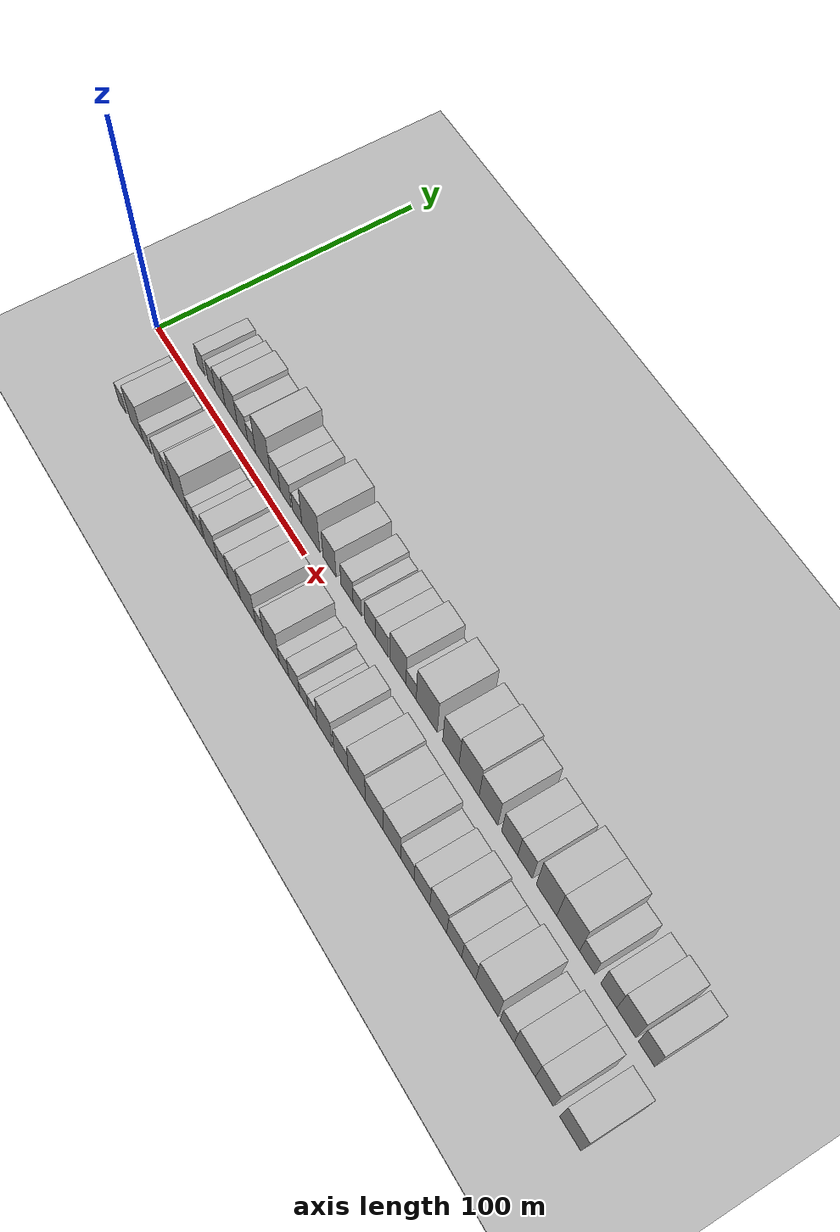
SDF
<?xml version="1.0" encoding="utf-8"?>

<sdf version="1.6">

   <world name="default">

      <gui fullscreen="0">

         <camera name="user_camera">

            <pose>-15 0 4.57585 0 0 0</pose>

            <view_controller>orbit</view_controller>

         </camera>

      </gui>

      <scene>

         <sky>

           <clouds>

             <speed>12</speed>

           </clouds>

         </sky>

         <ambient>0.4 0.4 0.4 1</ambient>

         <background>0.7 0.7 0.7 1</background>

         <shadows>1</shadows>

      </scene>

      <gravity>0 0 -9.8066</gravity>

      <magnetic_field>6e-06 2.3e-05 -4.2e-05</magnetic_field>

      <physics default="0" name="default_physics" type="ode">

         <ode>

            <solver>

               <type>quick</type>

               <iters>10</iters>

               <sor>1.0</sor>

               <use_dynamic_moi_rescaling>0</use_dynamic_moi_rescaling>

            </solver>

            <constraints>

               <cfm>0</cfm>

               <erp>0.2</erp>

               <contact_max_correcting_vel>100</contact_max_correcting_vel>

               <contact_surface_layer>0.001</contact_surface_layer>

            </constraints>

         </ode>

         <max_step_size>0.004</max_step_size>

         <real_time_factor>1</real_time_factor>

         <real_time_update_rate>250</real_time_update_rate>

      </physics>

      <light name="sun" type="directional">

         <cast_shadows>1</cast_shadows>

         <pose>0 0 10 0 0 0</pose>

         <diffuse>0.8 0.8 0.8 1</diffuse>

         <specular>0.2 0.2 0.2 1</specular>

         <attenuation>

            <range>1000</range>

            <constant>0.9</constant>

            <linear>0.01</linear>

            <quadratic>0.001</quadratic>

         </attenuation>

         <direction>-0.5 0.1 -0.9</direction>

      </light>

      <include>

         <name>ground_plane_1</name>

         <uri>model://HANNAS_ground_plane</uri>

         <pose>0 0 0  0 0 0</pose>

      </include>

      <include>

         <name>ground_plane_2</name>

         <uri>model://HANNAS_ground_plane</uri>

         <pose>100 0 0  0 0 0</pose>

      </include>

      <model name="building_1">

         <static>1</static>

         <pose frame="">22.7822 14.5000 0 0.000000 0.000000 1.570796</pose>

         <link name="link">

            <pose frame="">0 0 6.00 0 0 0</pose>

            <collision name="collision">

               <geometry>

                  <box>

                     <size>20.0000 5.5644 12.0000</size>

                  </box>

               </geometry>

               <max_contacts>10</max_contacts>

               <surface>

                  <contact>

                     <ode/>

                  </contact>

                  <bounce/>

                  <friction>

                     <torsional>

                        <ode/>

                     </torsional>

                     <ode/>

                  </friction>

               </surface>

            </collision>

            <visual name="visual">

               <cast_shadows>0</cast_shadows>

               <geometry>

                  <box>

                     <size>20.0000 5.5644 12.0000</size>

                  </box>

               </geometry>

               <material>

                  <script>

                     <uri>model://HANNAS_wall/materials/scripts</uri>

                     <uri>model://HANNAS_wall/materials/textures</uri>

                     <name>vrc/HANNAS_wall</name>

                  </script>

               </material>

            </visual>

            <self_collide>0</self_collide>

            <enable_wind>0</enable_wind>

            <kinematic>0</kinematic>

         </link>

      </model>

      <model name="building_2">

         <static>1</static>

         <pose frame="">30.2250 14.5000 0 0.000000 0.000000 1.570796</pose>

         <link name="link">

            <pose frame="">0 0 6.00 0 0 0</pose>

            <collision name="collision">

               <geometry>

                  <box>

                     <size>20.0000 5.3212 12.0000</size>

                  </box>

               </geometry>

               <max_contacts>10</max_contacts>

               <surface>

                  <contact>

                     <ode/>

                  </contact>

                  <bounce/>

                  <friction>

                     <torsional>

                        <ode/>

                     </torsional>

                     <ode/>

                  </friction>

               </surface>

            </collision>

            <visual name="visual">

               <cast_shadows>0</cast_shadows>

               <geometry>

                  <box>

                     <size>20.0000 5.3212 12.0000</size>

                  </box>

               </geometry>

               <material>

                  <script>

                     <uri>model://HANNAS_wall/materials/scripts</uri>

                     <uri>model://HANNAS_wall/materials/textures</uri>

                     <name>vrc/HANNAS_wall</name>

                  </script>

               </material>

            </visual>

            <self_collide>0</self_collide>

            <enable_wind>0</enable_wind>

            <kinematic>0</kinematic>

         </link>

      </model>

      <model name="building_3">

         <static>1</static>

         <pose frame="">36.3001 14.5000 0 0.000000 0.000000 1.570796</pose>

         <link name="link">

            <pose frame="">0 0 7.50 0 0 0</pose>

            <collision name="collision">

               <geometry>

                  <box>

                     <size>20.0000 6.8291 15.0000</size>

                  </box>

               </geometry>

               <max_contacts>10</max_contacts>

               <surface>

                  <contact>

                     <ode/>

                  </contact>

                  <bounce/>

                  <friction>

                     <torsional>

                        <ode/>

                     </torsional>

                     <ode/>

                  </friction>

               </surface>

            </collision>

            <visual name="visual">

               <cast_shadows>0</cast_shadows>

               <geometry>

                  <box>

                     <size>20.0000 6.8291 15.0000</size>

                  </box>

               </geometry>

               <material>

                  <script>

                     <uri>model://HANNAS_wall/materials/scripts</uri>

                     <uri>model://HANNAS_wall/materials/textures</uri>

                     <name>vrc/HANNAS_wall</name>

                  </script>

               </material>

            </visual>

            <self_collide>0</self_collide>

            <enable_wind>0</enable_wind>

            <kinematic>0</kinematic>

         </link>

      </model>

      <model name="building_4">

         <static>1</static>

         <pose frame="">43.8990 14.5000 0 0.000000 0.000000 1.570796</pose>

         <link name="link">

            <pose frame="">0 0 9.00 0 0 0</pose>

            <collision name="collision">

               <geometry>

                  <box>

                     <size>20.0000 8.3686 18.0000</size>

                  </box>

               </geometry>

               <max_contacts>10</max_contacts>

               <surface>

                  <contact>

                     <ode/>

                  </contact>

                  <bounce/>

                  <friction>

                     <torsional>

                        <ode/>

                     </torsional>

                     <ode/>

                  </friction>

               </surface>

            </collision>

            <visual name="visual">

               <cast_shadows>0</cast_shadows>

               <geometry>

                  <box>

                     <size>20.0000 8.3686 18.0000</size>

                  </box>

               </geometry>

               <material>

                  <script>

                     <uri>model://HANNAS_wall/materials/scripts</uri>

                     <uri>model://HANNAS_wall/materials/textures</uri>

                     <name>vrc/HANNAS_wall</name>

                  </script>

               </material>

            </visual>

            <self_collide>0</self_collide>

            <enable_wind>0</enable_wind>

            <kinematic>0</kinematic>

         </link>

      </model>

      <model name="building_5">

         <static>1</static>

         <pose frame="">51.5162 14.5000 0 0.000000 0.000000 1.570796</pose>

         <link name="link">

            <pose frame="">0 0 7.50 0 0 0</pose>

            <collision name="collision">

               <geometry>

                  <box>

                     <size>20.0000 6.8658 15.0000</size>

                  </box>

               </geometry>

               <max_contacts>10</max_contacts>

               <surface>

                  <contact>

                     <ode/>

                  </contact>

                  <bounce/>

                  <friction>

                     <torsional>

                        <ode/>

                     </torsional>

                     <ode/>

                  </friction>

               </surface>

            </collision>

            <visual name="visual">

               <cast_shadows>0</cast_shadows>

               <geometry>

                  <box>

                     <size>20.0000 6.8658 15.0000</size>

                  </box>

               </geometry>

               <material>

                  <script>

                     <uri>model://HANNAS_wall/materials/scripts</uri>

                     <uri>model://HANNAS_wall/materials/textures</uri>

                     <name>vrc/HANNAS_wall</name>

                  </script>

               </material>

            </visual>

            <self_collide>0</self_collide>

            <enable_wind>0</enable_wind>

            <kinematic>0</kinematic>

         </link>

      </model>

      <model name="building_6">

         <static>1</static>

         <pose frame="">57.6712 14.5000 0 0.000000 0.000000 1.570796</pose>

         <link name="link">

            <pose frame="">0 0 6.00 0 0 0</pose>

            <collision name="collision">

               <geometry>

                  <box>

                     <size>20.0000 5.4442 12.0000</size>

                  </box>

               </geometry>

               <max_contacts>10</max_contacts>

               <surface>

                  <contact>

                     <ode/>

                  </contact>

                  <bounce/>

                  <friction>

                     <torsional>

                        <ode/>

                     </torsional>

                     <ode/>

                  </friction>

               </surface>

            </collision>

            <visual name="visual">

               <cast_shadows>0</cast_shadows>

               <geometry>

                  <box>

                     <size>20.0000 5.4442 12.0000</size>

                  </box>

               </geometry>

               <material>

                  <script>

                     <uri>model://HANNAS_wall/materials/scripts</uri>

                     <uri>model://HANNAS_wall/materials/textures</uri>

                     <name>vrc/HANNAS_wall</name>

                  </script>

               </material>

            </visual>

            <self_collide>0</self_collide>

            <enable_wind>0</enable_wind>

            <kinematic>0</kinematic>

         </link>

      </model>

      <model name="building_7">

         <static>1</static>

         <pose frame="">65.3493 14.5000 0 0.000000 0.000000 1.570796</pose>

         <link name="link">

            <pose frame="">0 0 12.00 0 0 0</pose>

            <collision name="collision">

               <geometry>

                  <box>

                     <size>20.0000 9.9121 24.0000</size>

                  </box>

               </geometry>

               <max_contacts>10</max_contacts>

               <surface>

                  <contact>

                     <ode/>

                  </contact>

                  <bounce/>

                  <friction>

                     <torsional>

                        <ode/>

                     </torsional>

                     <ode/>

                  </friction>

               </surface>

            </collision>

            <visual name="visual">

               <cast_shadows>0</cast_shadows>

               <geometry>

                  <box>

                     <size>20.0000 9.9121 24.0000</size>

                  </box>

               </geometry>

               <material>

                  <script>

                     <uri>model://HANNAS_wall/materials/scripts</uri>

                     <uri>model://HANNAS_wall/materials/textures</uri>

                     <name>vrc/HANNAS_wall</name>

                  </script>

               </material>

            </visual>

            <self_collide>0</self_collide>

            <enable_wind>0</enable_wind>

            <kinematic>0</kinematic>

         </link>

      </model>

      <model name="building_8">

         <static>1</static>

         <pose frame="">73.4739 14.5000 0 0.000000 0.000000 1.570796</pose>

         <link name="link">

            <pose frame="">0 0 7.50 0 0 0</pose>

            <collision name="collision">

               <geometry>

                  <box>

                     <size>20.0000 6.3371 15.0000</size>

                  </box>

               </geometry>

               <max_contacts>10</max_contacts>

               <surface>

                  <contact>

                     <ode/>

                  </contact>

                  <bounce/>

                  <friction>

                     <torsional>

                        <ode/>

                     </torsional>

                     <ode/>

                  </friction>

               </surface>

            </collision>

            <visual name="visual">

               <cast_shadows>0</cast_shadows>

               <geometry>

                  <box>

                     <size>20.0000 6.3371 15.0000</size>

                  </box>

               </geometry>

               <material>

                  <script>

                     <uri>model://HANNAS_wall/materials/scripts</uri>

                     <uri>model://HANNAS_wall/materials/textures</uri>

                     <name>vrc/HANNAS_wall</name>

                  </script>

               </material>

            </visual>

            <self_collide>0</self_collide>

            <enable_wind>0</enable_wind>

            <kinematic>0</kinematic>

         </link>

      </model>

      <model name="building_9">

         <static>1</static>

         <pose frame="">80.1584 14.5000 0 0.000000 0.000000 1.570796</pose>

         <link name="link">

            <pose frame="">0 0 7.50 0 0 0</pose>

            <collision name="collision">

               <geometry>

                  <box>

                     <size>20.0000 7.0319 15.0000</size>

                  </box>

               </geometry>

               <max_contacts>10</max_contacts>

               <surface>

                  <contact>

                     <ode/>

                  </contact>

                  <bounce/>

                  <friction>

                     <torsional>

                        <ode/>

                     </torsional>

                     <ode/>

                  </friction>

               </surface>

            </collision>

            <visual name="visual">

               <cast_shadows>0</cast_shadows>

               <geometry>

                  <box>

                     <size>20.0000 7.0319 15.0000</size>

                  </box>

               </geometry>

               <material>

                  <script>

                     <uri>model://HANNAS_wall/materials/scripts</uri>

                     <uri>model://HANNAS_wall/materials/textures</uri>

                     <name>vrc/HANNAS_wall</name>

                  </script>

               </material>

            </visual>

            <self_collide>0</self_collide>

            <enable_wind>0</enable_wind>

            <kinematic>0</kinematic>

         </link>

      </model>

      <model name="building_10">

         <static>1</static>

         <pose frame="">87.6701 14.5000 0 0.000000 0.000000 1.570796</pose>

         <link name="link">

            <pose frame="">0 0 6.00 0 0 0</pose>

            <collision name="collision">

               <geometry>

                  <box>

                     <size>20.0000 5.9915 12.0000</size>

                  </box>

               </geometry>

               <max_contacts>10</max_contacts>

               <surface>

                  <contact>

                     <ode/>

                  </contact>

                  <bounce/>

                  <friction>

                     <torsional>

                        <ode/>

                     </torsional>

                     <ode/>

                  </friction>

               </surface>

            </collision>

            <visual name="visual">

               <cast_shadows>0</cast_shadows>

               <geometry>

                  <box>

                     <size>20.0000 5.9915 12.0000</size>

                  </box>

               </geometry>

               <material>

                  <script>

                     <uri>model://HANNAS_wall/materials/scripts</uri>

                     <uri>model://HANNAS_wall/materials/textures</uri>

                     <name>vrc/HANNAS_wall</name>

                  </script>

               </material>

            </visual>

            <self_collide>0</self_collide>

            <enable_wind>0</enable_wind>

            <kinematic>0</kinematic>

         </link>

      </model>

      <model name="building_11">

         <static>1</static>

         <pose frame="">96.3384 14.5000 0 0.000000 0.000000 1.570796</pose>

         <link name="link">

            <pose frame="">0 0 12.00 0 0 0</pose>

            <collision name="collision">

               <geometry>

                  <box>

                     <size>20.0000 11.3453 24.0000</size>

                  </box>

               </geometry>

               <max_contacts>10</max_contacts>

               <surface>

                  <contact>

                     <ode/>

                  </contact>

                  <bounce/>

                  <friction>

                     <torsional>

                        <ode/>

                     </torsional>

                     <ode/>

                  </friction>

               </surface>

            </collision>

            <visual name="visual">

               <cast_shadows>0</cast_shadows>

               <geometry>

                  <box>

                     <size>20.0000 11.3453 24.0000</size>

                  </box>

               </geometry>

               <material>

                  <script>

                     <uri>model://HANNAS_wall/materials/scripts</uri>

                     <uri>model://HANNAS_wall/materials/textures</uri>

                     <name>vrc/HANNAS_wall</name>

                  </script>

               </material>

            </visual>

            <self_collide>0</self_collide>

            <enable_wind>0</enable_wind>

            <kinematic>0</kinematic>

         </link>

      </model>

      <model name="building_12">

         <static>1</static>

         <pose frame="">108.0705 14.5000 0 0.000000 0.000000 1.570796</pose>

         <link name="link">

            <pose frame="">0 0 9.00 0 0 0</pose>

            <collision name="collision">

               <geometry>

                  <box>

                     <size>20.0000 8.1189 18.0000</size>

                  </box>

               </geometry>

               <max_contacts>10</max_contacts>

               <surface>

                  <contact>

                     <ode/>

                  </contact>

                  <bounce/>

                  <friction>

                     <torsional>

                        <ode/>

                     </torsional>

                     <ode/>

                  </friction>

               </surface>

            </collision>

            <visual name="visual">

               <cast_shadows>0</cast_shadows>

               <geometry>

                  <box>

                     <size>20.0000 8.1189 18.0000</size>

                  </box>

               </geometry>

               <material>

                  <script>

                     <uri>model://HANNAS_wall/materials/scripts</uri>

                     <uri>model://HANNAS_wall/materials/textures</uri>

                     <name>vrc/HANNAS_wall</name>

                  </script>

               </material>

            </visual>

            <self_collide>0</self_collide>

            <enable_wind>0</enable_wind>

            <kinematic>0</kinematic>

         </link>

      </model>

      <model name="building_13">

         <static>1</static>

         <pose frame="">118.8091 14.5000 0 0.000000 0.000000 1.570796</pose>

         <link name="link">

            <pose frame="">0 0 7.50 0 0 0</pose>

            <collision name="collision">

               <geometry>

                  <box>

                     <size>20.0000 7.3583 15.0000</size>

                  </box>

               </geometry>

               <max_contacts>10</max_contacts>

               <surface>

                  <contact>

                     <ode/>

                  </contact>

                  <bounce/>

                  <friction>

                     <torsional>

                        <ode/>

                     </torsional>

                     <ode/>

                  </friction>

               </surface>

            </collision>

            <visual name="visual">

               <cast_shadows>0</cast_shadows>

               <geometry>

                  <box>

                     <size>20.0000 7.3583 15.0000</size>

                  </box>

               </geometry>

               <material>

                  <script>

                     <uri>model://HANNAS_wall/materials/scripts</uri>

                     <uri>model://HANNAS_wall/materials/textures</uri>

                     <name>vrc/HANNAS_wall</name>

                  </script>

               </material>

            </visual>

            <self_collide>0</self_collide>

            <enable_wind>0</enable_wind>

            <kinematic>0</kinematic>

         </link>

      </model>

      <model name="building_14">

         <static>1</static>

         <pose frame="">125.0495 14.5000 0 0.000000 0.000000 1.570796</pose>

         <link name="link">

            <pose frame="">0 0 6.00 0 0 0</pose>

            <collision name="collision">

               <geometry>

                  <box>

                     <size>20.0000 5.1225 12.0000</size>

                  </box>

               </geometry>

               <max_contacts>10</max_contacts>

               <surface>

                  <contact>

                     <ode/>

                  </contact>

                  <bounce/>

                  <friction>

                     <torsional>

                        <ode/>

                     </torsional>

                     <ode/>

                  </friction>

               </surface>

            </collision>

            <visual name="visual">

               <cast_shadows>0</cast_shadows>

               <geometry>

                  <box>

                     <size>20.0000 5.1225 12.0000</size>

                  </box>

               </geometry>

               <material>

                  <script>

                     <uri>model://HANNAS_wall/materials/scripts</uri>

                     <uri>model://HANNAS_wall/materials/textures</uri>

                     <name>vrc/HANNAS_wall</name>

                  </script>

               </material>

            </visual>

            <self_collide>0</self_collide>

            <enable_wind>0</enable_wind>

            <kinematic>0</kinematic>

         </link>

      </model>

      <model name="building_15">

         <static>1</static>

         <pose frame="">132.8658 14.5000 0 0.000000 0.000000 1.570796</pose>

         <link name="link">

            <pose frame="">0 0 7.50 0 0 0</pose>

            <collision name="collision">

               <geometry>

                  <box>

                     <size>20.0000 6.5102 15.0000</size>

                  </box>

               </geometry>

               <max_contacts>10</max_contacts>

               <surface>

                  <contact>

                     <ode/>

                  </contact>

                  <bounce/>

                  <friction>

                     <torsional>

                        <ode/>

                     </torsional>

                     <ode/>

                  </friction>

               </surface>

            </collision>

            <visual name="visual">

               <cast_shadows>0</cast_shadows>

               <geometry>

                  <box>

                     <size>20.0000 6.5102 15.0000</size>

                  </box>

               </geometry>

               <material>

                  <script>

                     <uri>model://HANNAS_wall/materials/scripts</uri>

                     <uri>model://HANNAS_wall/materials/textures</uri>

                     <name>vrc/HANNAS_wall</name>

                  </script>

               </material>

            </visual>

            <self_collide>0</self_collide>

            <enable_wind>0</enable_wind>

            <kinematic>0</kinematic>

         </link>

      </model>

      <model name="building_16">

         <static>1</static>

         <pose frame="">139.8515 14.5000 0 0.000000 0.000000 1.570796</pose>

         <link name="link">

            <pose frame="">0 0 7.50 0 0 0</pose>

            <collision name="collision">

               <geometry>

                  <box>

                     <size>20.0000 7.4613 15.0000</size>

                  </box>

               </geometry>

               <max_contacts>10</max_contacts>

               <surface>

                  <contact>

                     <ode/>

                  </contact>

                  <bounce/>

                  <friction>

                     <torsional>

                        <ode/>

                     </torsional>

                     <ode/>

                  </friction>

               </surface>

            </collision>

            <visual name="visual">

               <cast_shadows>0</cast_shadows>

               <geometry>

                  <box>

                     <size>20.0000 7.4613 15.0000</size>

                  </box>

               </geometry>

               <material>

                  <script>

                     <uri>model://HANNAS_wall/materials/scripts</uri>

                     <uri>model://HANNAS_wall/materials/textures</uri>

                     <name>vrc/HANNAS_wall</name>

                  </script>

               </material>

            </visual>

            <self_collide>0</self_collide>

            <enable_wind>0</enable_wind>

            <kinematic>0</kinematic>

         </link>

      </model>

      <model name="building_17">

         <static>1</static>

         <pose frame="">149.2267 14.5000 0 0.000000 0.000000 1.570796</pose>

         <link name="link">

            <pose frame="">0 0 10.50 0 0 0</pose>

            <collision name="collision">

               <geometry>

                  <box>

                     <size>20.0000 9.2890 21.0000</size>

                  </box>

               </geometry>

               <max_contacts>10</max_contacts>

               <surface>

                  <contact>

                     <ode/>

                  </contact>

                  <bounce/>

                  <friction>

                     <torsional>

                        <ode/>

                     </torsional>

                     <ode/>

                  </friction>

               </surface>

            </collision>

            <visual name="visual">

               <cast_shadows>0</cast_shadows>

               <geometry>

                  <box>

                     <size>20.0000 9.2890 21.0000</size>

                  </box>

               </geometry>

               <material>

                  <script>

                     <uri>model://HANNAS_wall/materials/scripts</uri>

                     <uri>model://HANNAS_wall/materials/textures</uri>

                     <name>vrc/HANNAS_wall</name>

                  </script>

               </material>

            </visual>

            <self_collide>0</self_collide>

            <enable_wind>0</enable_wind>

            <kinematic>0</kinematic>

         </link>

      </model>

      <model name="building_18">

         <static>1</static>

         <pose frame="">156.8171 14.5000 0 0.000000 0.000000 1.570796</pose>

         <link name="link">

            <pose frame="">0 0 6.00 0 0 0</pose>

            <collision name="collision">

               <geometry>

                  <box>

                     <size>20.0000 5.8918 12.0000</size>

                  </box>

               </geometry>

               <max_contacts>10</max_contacts>

               <surface>

                  <contact>

                     <ode/>

                  </contact>

                  <bounce/>

                  <friction>

                     <torsional>

                        <ode/>

                     </torsional>

                     <ode/>

                  </friction>

               </surface>

            </collision>

            <visual name="visual">

               <cast_shadows>0</cast_shadows>

               <geometry>

                  <box>

                     <size>20.0000 5.8918 12.0000</size>

                  </box>

               </geometry>

               <material>

                  <script>

                     <uri>model://HANNAS_wall/materials/scripts</uri>

                     <uri>model://HANNAS_wall/materials/textures</uri>

                     <name>vrc/HANNAS_wall</name>

                  </script>

               </material>

            </visual>

            <self_collide>0</self_collide>

            <enable_wind>0</enable_wind>

            <kinematic>0</kinematic>

         </link>

      </model>

      <model name="building_19">

         <static>1</static>

         <pose frame="">165.7413 14.5000 0 0.000000 0.000000 1.570796</pose>

         <link name="link">

            <pose frame="">0 0 12.00 0 0 0</pose>

            <collision name="collision">

               <geometry>

                  <box>

                     <size>20.0000 11.9566 24.0000</size>

                  </box>

               </geometry>

               <max_contacts>10</max_contacts>

               <surface>

                  <contact>

                     <ode/>

                  </contact>

                  <bounce/>

                  <friction>

                     <torsional>

                        <ode/>

                     </torsional>

                     <ode/>

                  </friction>

               </surface>

            </collision>

            <visual name="visual">

               <cast_shadows>0</cast_shadows>

               <geometry>

                  <box>

                     <size>20.0000 11.9566 24.0000</size>

                  </box>

               </geometry>

               <material>

                  <script>

                     <uri>model://HANNAS_wall/materials/scripts</uri>

                     <uri>model://HANNAS_wall/materials/textures</uri>

                     <name>vrc/HANNAS_wall</name>

                  </script>

               </material>

            </visual>

            <self_collide>0</self_collide>

            <enable_wind>0</enable_wind>

            <kinematic>0</kinematic>

         </link>

      </model>

      <model name="building_20">

         <static>1</static>

         <pose frame="">179.2212 14.5000 0 0.000000 0.000000 1.570796</pose>

         <link name="link">

            <pose frame="">0 0 10.50 0 0 0</pose>

            <collision name="collision">

               <geometry>

                  <box>

                     <size>20.0000 9.0032 21.0000</size>

                  </box>

               </geometry>

               <max_contacts>10</max_contacts>

               <surface>

                  <contact>

                     <ode/>

                  </contact>

                  <bounce/>

                  <friction>

                     <torsional>

                        <ode/>

                     </torsional>

                     <ode/>

                  </friction>

               </surface>

            </collision>

            <visual name="visual">

               <cast_shadows>0</cast_shadows>

               <geometry>

                  <box>

                     <size>20.0000 9.0032 21.0000</size>

                  </box>

               </geometry>

               <material>

                  <script>

                     <uri>model://HANNAS_wall/materials/scripts</uri>

                     <uri>model://HANNAS_wall/materials/textures</uri>

                     <name>vrc/HANNAS_wall</name>

                  </script>

               </material>

            </visual>

            <self_collide>0</self_collide>

            <enable_wind>0</enable_wind>

            <kinematic>0</kinematic>

         </link>

      </model>

      <model name="building_21">

         <static>1</static>

         <pose frame="">189.2372 14.5000 0 0.000000 0.000000 1.570796</pose>

         <link name="link">

            <pose frame="">0 0 12.00 0 0 0</pose>

            <collision name="collision">

               <geometry>

                  <box>

                     <size>20.0000 11.0289 24.0000</size>

                  </box>

               </geometry>

               <max_contacts>10</max_contacts>

               <surface>

                  <contact>

                     <ode/>

                  </contact>

                  <bounce/>

                  <friction>

                     <torsional>

                        <ode/>

                     </torsional>

                     <ode/>

                  </friction>

               </surface>

            </collision>

            <visual name="visual">

               <cast_shadows>0</cast_shadows>

               <geometry>

                  <box>

                     <size>20.0000 11.0289 24.0000</size>

                  </box>

               </geometry>

               <material>

                  <script>

                     <uri>model://HANNAS_wall/materials/scripts</uri>

                     <uri>model://HANNAS_wall/materials/textures</uri>

                     <name>vrc/HANNAS_wall</name>

                  </script>

               </material>

            </visual>

            <self_collide>0</self_collide>

            <enable_wind>0</enable_wind>

            <kinematic>0</kinematic>

         </link>

      </model>

      <model name="building_22">

         <static>1</static>

         <pose frame="">199.7666 14.5000 0 0.000000 0.000000 1.570796</pose>

         <link name="link">

            <pose frame="">0 0 10.50 0 0 0</pose>

            <collision name="collision">

               <geometry>

                  <box>

                     <size>20.0000 10.0298 21.0000</size>

                  </box>

               </geometry>

               <max_contacts>10</max_contacts>

               <surface>

                  <contact>

                     <ode/>

                  </contact>

                  <bounce/>

                  <friction>

                     <torsional>

                        <ode/>

                     </torsional>

                     <ode/>

                  </friction>

               </surface>

            </collision>

            <visual name="visual">

               <cast_shadows>0</cast_shadows>

               <geometry>

                  <box>

                     <size>20.0000 10.0298 21.0000</size>

                  </box>

               </geometry>

               <material>

                  <script>

                     <uri>model://HANNAS_wall/materials/scripts</uri>

                     <uri>model://HANNAS_wall/materials/textures</uri>

                     <name>vrc/HANNAS_wall</name>

                  </script>

               </material>

            </visual>

            <self_collide>0</self_collide>

            <enable_wind>0</enable_wind>

            <kinematic>0</kinematic>

         </link>

      </model>

      <model name="building_23">

         <static>1</static>

         <pose frame="">211.0317 14.5000 0 0.000000 0.000000 1.570796</pose>

         <link name="link">

            <pose frame="">0 0 9.00 0 0 0</pose>

            <collision name="collision">

               <geometry>

                  <box>

                     <size>20.0000 8.5003 18.0000</size>

                  </box>

               </geometry>

               <max_contacts>10</max_contacts>

               <surface>

                  <contact>

                     <ode/>

                  </contact>

                  <bounce/>

                  <friction>

                     <torsional>

                        <ode/>

                     </torsional>

                     <ode/>

                  </friction>

               </surface>

            </collision>

            <visual name="visual">

               <cast_shadows>0</cast_shadows>

               <geometry>

                  <box>

                     <size>20.0000 8.5003 18.0000</size>

                  </box>

               </geometry>

               <material>

                  <script>

                     <uri>model://HANNAS_wall/materials/scripts</uri>

                     <uri>model://HANNAS_wall/materials/textures</uri>

                     <name>vrc/HANNAS_wall</name>

                  </script>

               </material>

            </visual>

            <self_collide>0</self_collide>

            <enable_wind>0</enable_wind>

            <kinematic>0</kinematic>

         </link>

      </model>

      <model name="building_24">

         <static>1</static>

         <pose frame="">219.0821 14.5000 0 0.000000 0.000000 1.570796</pose>

         <link name="link">

            <pose frame="">0 0 9.00 0 0 0</pose>

            <collision name="collision">

               <geometry>

                  <box>

                     <size>20.0000 7.6005 18.0000</size>

                  </box>

               </geometry>

               <max_contacts>10</max_contacts>

               <surface>

                  <contact>

                     <ode/>

                  </contact>

                  <bounce/>

                  <friction>

                     <torsional>

                        <ode/>

                     </torsional>

                     <ode/>

                  </friction>

               </surface>

            </collision>

            <visual name="visual">

               <cast_shadows>0</cast_shadows>

               <geometry>

                  <box>

                     <size>20.0000 7.6005 18.0000</size>

                  </box>

               </geometry>

               <material>

                  <script>

                     <uri>model://HANNAS_wall/materials/scripts</uri>

                     <uri>model://HANNAS_wall/materials/textures</uri>

                     <name>vrc/HANNAS_wall</name>

                  </script>

               </material>

            </visual>

            <self_collide>0</self_collide>

            <enable_wind>0</enable_wind>

            <kinematic>0</kinematic>

         </link>

      </model>

      <model name="building_25">

         <static>1</static>

         <pose frame="">230.1089 14.5000 0 0.000000 0.000000 1.570796</pose>

         <link name="link">

            <pose frame="">0 0 12.00 0 0 0</pose>

            <collision name="collision">

               <geometry>

                  <box>

                     <size>20.0000 10.4532 24.0000</size>

                  </box>

               </geometry>

               <max_contacts>10</max_contacts>

               <surface>

                  <contact>

                     <ode/>

                  </contact>

                  <bounce/>

                  <friction>

                     <torsional>

                        <ode/>

                     </torsional>

                     <ode/>

                  </friction>

               </surface>

            </collision>

            <visual name="visual">

               <cast_shadows>0</cast_shadows>

               <geometry>

                  <box>

                     <size>20.0000 10.4532 24.0000</size>

                  </box>

               </geometry>

               <material>

                  <script>

                     <uri>model://HANNAS_wall/materials/scripts</uri>

                     <uri>model://HANNAS_wall/materials/textures</uri>

                     <name>vrc/HANNAS_wall</name>

                  </script>

               </material>

            </visual>

            <self_collide>0</self_collide>

            <enable_wind>0</enable_wind>

            <kinematic>0</kinematic>

         </link>

      </model>

      <model name="building_26">

         <static>1</static>

         <pose frame="">241.0479 14.5000 0 0.000000 0.000000 1.570796</pose>

         <link name="link">

            <pose frame="">0 0 12.00 0 0 0</pose>

            <collision name="collision">

               <geometry>

                  <box>

                     <size>20.0000 11.4248 24.0000</size>

                  </box>

               </geometry>

               <max_contacts>10</max_contacts>

               <surface>

                  <contact>

                     <ode/>

                  </contact>

                  <bounce/>

                  <friction>

                     <torsional>

                        <ode/>

                     </torsional>

                     <ode/>

                  </friction>

               </surface>

            </collision>

            <visual name="visual">

               <cast_shadows>0</cast_shadows>

               <geometry>

                  <box>

                     <size>20.0000 11.4248 24.0000</size>

                  </box>

               </geometry>

               <material>

                  <script>

                     <uri>model://HANNAS_wall/materials/scripts</uri>

                     <uri>model://HANNAS_wall/materials/textures</uri>

                     <name>vrc/HANNAS_wall</name>

                  </script>

               </material>

            </visual>

            <self_collide>0</self_collide>

            <enable_wind>0</enable_wind>

            <kinematic>0</kinematic>

         </link>

      </model>

      <model name="building_27">

         <static>1</static>

         <pose frame="">250.4484 14.5000 0 0.000000 0.000000 1.570796</pose>

         <link name="link">

            <pose frame="">0 0 7.50 0 0 0</pose>

            <collision name="collision">

               <geometry>

                  <box>

                     <size>20.0000 7.3761 15.0000</size>

                  </box>

               </geometry>

               <max_contacts>10</max_contacts>

               <surface>

                  <contact>

                     <ode/>

                  </contact>

                  <bounce/>

                  <friction>

                     <torsional>

                        <ode/>

                     </torsional>

                     <ode/>

                  </friction>

               </surface>

            </collision>

            <visual name="visual">

               <cast_shadows>0</cast_shadows>

               <geometry>

                  <box>

                     <size>20.0000 7.3761 15.0000</size>

                  </box>

               </geometry>

               <material>

                  <script>

                     <uri>model://HANNAS_wall/materials/scripts</uri>

                     <uri>model://HANNAS_wall/materials/textures</uri>

                     <name>vrc/HANNAS_wall</name>

                  </script>

               </material>

            </visual>

            <self_collide>0</self_collide>

            <enable_wind>0</enable_wind>

            <kinematic>0</kinematic>

         </link>

      </model>

      <model name="building_28">

         <static>1</static>

         <pose frame="">260.9795 14.5000 0 0.000000 0.000000 1.570796</pose>

         <link name="link">

            <pose frame="">0 0 9.00 0 0 0</pose>

            <collision name="collision">

               <geometry>

                  <box>

                     <size>20.0000 7.6862 18.0000</size>

                  </box>

               </geometry>

               <max_contacts>10</max_contacts>

               <surface>

                  <contact>

                     <ode/>

                  </contact>

                  <bounce/>

                  <friction>

                     <torsional>

                        <ode/>

                     </torsional>

                     <ode/>

                  </friction>

               </surface>

            </collision>

            <visual name="visual">

               <cast_shadows>0</cast_shadows>

               <geometry>

                  <box>

                     <size>20.0000 7.6862 18.0000</size>

                  </box>

               </geometry>

               <material>

                  <script>

                     <uri>model://HANNAS_wall/materials/scripts</uri>

                     <uri>model://HANNAS_wall/materials/textures</uri>

                     <name>vrc/HANNAS_wall</name>

                  </script>

               </material>

            </visual>

            <self_collide>0</self_collide>

            <enable_wind>0</enable_wind>

            <kinematic>0</kinematic>

         </link>

      </model>

      <model name="building_29">

         <static>1</static>

         <pose frame="">269.4135 14.5000 0 0.000000 0.000000 1.570796</pose>

         <link name="link">

            <pose frame="">0 0 10.50 0 0 0</pose>

            <collision name="collision">

               <geometry>

                  <box>

                     <size>20.0000 9.1818 21.0000</size>

                  </box>

               </geometry>

               <max_contacts>10</max_contacts>

               <surface>

                  <contact>

                     <ode/>

                  </contact>

                  <bounce/>

                  <friction>

                     <torsional>

                        <ode/>

                     </torsional>

                     <ode/>

                  </friction>

               </surface>

            </collision>

            <visual name="visual">

               <cast_shadows>0</cast_shadows>

               <geometry>

                  <box>

                     <size>20.0000 9.1818 21.0000</size>

                  </box>

               </geometry>

               <material>

                  <script>

                     <uri>model://HANNAS_wall/materials/scripts</uri>

                     <uri>model://HANNAS_wall/materials/textures</uri>

                     <name>vrc/HANNAS_wall</name>

                  </script>

               </material>

            </visual>

            <self_collide>0</self_collide>

            <enable_wind>0</enable_wind>

            <kinematic>0</kinematic>

         </link>

      </model>

      <model name="building_30">

         <static>1</static>

         <pose frame="">278.8989 14.5000 0 0.000000 0.000000 1.570796</pose>

         <link name="link">

            <pose frame="">0 0 9.00 0 0 0</pose>

            <collision name="collision">

               <geometry>

                  <box>

                     <size>20.0000 7.7890 18.0000</size>

                  </box>

               </geometry>

               <max_contacts>10</max_contacts>

               <surface>

                  <contact>

                     <ode/>

                  </contact>

                  <bounce/>

                  <friction>

                     <torsional>

                        <ode/>

                     </torsional>

                     <ode/>

                  </friction>

               </surface>

            </collision>

            <visual name="visual">

               <cast_shadows>0</cast_shadows>

               <geometry>

                  <box>

                     <size>20.0000 7.7890 18.0000</size>

                  </box>

               </geometry>

               <material>

                  <script>

                     <uri>model://HANNAS_wall/materials/scripts</uri>

                     <uri>model://HANNAS_wall/materials/textures</uri>

                     <name>vrc/HANNAS_wall</name>

                  </script>

               </material>

            </visual>

            <self_collide>0</self_collide>

            <enable_wind>0</enable_wind>

            <kinematic>0</kinematic>

         </link>

      </model>

      <model name="building_31">

         <static>1</static>

         <pose frame="">22.6875 -14.5000 0 0.000000 0.000000 1.570796</pose>

         <link name="link">

            <pose frame="">0 0 6.00 0 0 0</pose>

            <collision name="collision">

               <geometry>

                  <box>

                     <size>20.0000 5.3750 12.0000</size>

                  </box>

               </geometry>

               <max_contacts>10</max_contacts>

               <surface>

                  <contact>

                     <ode/>

                  </contact>

                  <bounce/>

                  <friction>

                     <torsional>

                        <ode/>

                     </torsional>

                     <ode/>

                  </friction>

               </surface>

            </collision>

            <visual name="visual">

               <cast_shadows>0</cast_shadows>

               <geometry>

                  <box>

                     <size>20.0000 5.3750 12.0000</size>

                  </box>

               </geometry>

               <material>

                  <script>

                     <uri>model://HANNAS_wall/materials/scripts</uri>

                     <uri>model://HANNAS_wall/materials/textures</uri>

                     <name>vrc/HANNAS_wall</name>

                  </script>

               </material>

            </visual>

            <self_collide>0</self_collide>

            <enable_wind>0</enable_wind>

            <kinematic>0</kinematic>

         </link>

      </model>

      <model name="building_32">

         <static>1</static>

         <pose frame="">33.0298 -14.5000 0 0.000000 0.000000 1.570796</pose>

         <link name="link">

            <pose frame="">0 0 10.50 0 0 0</pose>

            <collision name="collision">

               <geometry>

                  <box>

                     <size>20.0000 9.3095 21.0000</size>

                  </box>

               </geometry>

               <max_contacts>10</max_contacts>

               <surface>

                  <contact>

                     <ode/>

                  </contact>

                  <bounce/>

                  <friction>

                     <torsional>

                        <ode/>

                     </torsional>

                     <ode/>

                  </friction>

               </surface>

            </collision>

            <visual name="visual">

               <cast_shadows>0</cast_shadows>

               <geometry>

                  <box>

                     <size>20.0000 9.3095 21.0000</size>

                  </box>

               </geometry>

               <material>

                  <script>

                     <uri>model://HANNAS_wall/materials/scripts</uri>

                     <uri>model://HANNAS_wall/materials/textures</uri>

                     <name>vrc/HANNAS_wall</name>

                  </script>

               </material>

            </visual>

            <self_collide>0</self_collide>

            <enable_wind>0</enable_wind>

            <kinematic>0</kinematic>

         </link>

      </model>

      <model name="building_33">

         <static>1</static>

         <pose frame="">40.4763 -14.5000 0 0.000000 0.000000 1.570796</pose>

         <link name="link">

            <pose frame="">0 0 6.00 0 0 0</pose>

            <collision name="collision">

               <geometry>

                  <box>

                     <size>20.0000 5.5835 12.0000</size>

                  </box>

               </geometry>

               <max_contacts>10</max_contacts>

               <surface>

                  <contact>

                     <ode/>

                  </contact>

                  <bounce/>

                  <friction>

                     <torsional>

                        <ode/>

                     </torsional>

                     <ode/>

                  </friction>

               </surface>

            </collision>

            <visual name="visual">

               <cast_shadows>0</cast_shadows>

               <geometry>

                  <box>

                     <size>20.0000 5.5835 12.0000</size>

                  </box>

               </geometry>

               <material>

                  <script>

                     <uri>model://HANNAS_wall/materials/scripts</uri>

                     <uri>model://HANNAS_wall/materials/textures</uri>

                     <name>vrc/HANNAS_wall</name>

                  </script>

               </material>

            </visual>

            <self_collide>0</self_collide>

            <enable_wind>0</enable_wind>

            <kinematic>0</kinematic>

         </link>

      </model>

      <model name="building_34">

         <static>1</static>

         <pose frame="">49.4508 -14.5000 0 0.000000 0.000000 1.570796</pose>

         <link name="link">

            <pose frame="">0 0 7.50 0 0 0</pose>

            <collision name="collision">

               <geometry>

                  <box>

                     <size>20.0000 6.3654 15.0000</size>

                  </box>

               </geometry>

               <max_contacts>10</max_contacts>

               <surface>

                  <contact>

                     <ode/>

                  </contact>

                  <bounce/>

                  <friction>

                     <torsional>

                        <ode/>

                     </torsional>

                     <ode/>

                  </friction>

               </surface>

            </collision>

            <visual name="visual">

               <cast_shadows>0</cast_shadows>

               <geometry>

                  <box>

                     <size>20.0000 6.3654 15.0000</size>

                  </box>

               </geometry>

               <material>

                  <script>

                     <uri>model://HANNAS_wall/materials/scripts</uri>

                     <uri>model://HANNAS_wall/materials/textures</uri>

                     <name>vrc/HANNAS_wall</name>

                  </script>

               </material>

            </visual>

            <self_collide>0</self_collide>

            <enable_wind>0</enable_wind>

            <kinematic>0</kinematic>

         </link>

      </model>

      <model name="building_35">

         <static>1</static>

         <pose frame="">55.6655 -14.5000 0 0.000000 0.000000 1.570796</pose>

         <link name="link">

            <pose frame="">0 0 7.50 0 0 0</pose>

            <collision name="collision">

               <geometry>

                  <box>

                     <size>20.0000 6.0639 15.0000</size>

                  </box>

               </geometry>

               <max_contacts>10</max_contacts>

               <surface>

                  <contact>

                     <ode/>

                  </contact>

                  <bounce/>

                  <friction>

                     <torsional>

                        <ode/>

                     </torsional>

                     <ode/>

                  </friction>

               </surface>

            </collision>

            <visual name="visual">

               <cast_shadows>0</cast_shadows>

               <geometry>

                  <box>

                     <size>20.0000 6.0639 15.0000</size>

                  </box>

               </geometry>

               <material>

                  <script>

                     <uri>model://HANNAS_wall/materials/scripts</uri>

                     <uri>model://HANNAS_wall/materials/textures</uri>

                     <name>vrc/HANNAS_wall</name>

                  </script>

               </material>

            </visual>

            <self_collide>0</self_collide>

            <enable_wind>0</enable_wind>

            <kinematic>0</kinematic>

         </link>

      </model>

      <model name="building_36">

         <static>1</static>

         <pose frame="">63.7244 -14.5000 0 0.000000 0.000000 1.570796</pose>

         <link name="link">

            <pose frame="">0 0 12.00 0 0 0</pose>

            <collision name="collision">

               <geometry>

                  <box>

                     <size>20.0000 10.0539 24.0000</size>

                  </box>

               </geometry>

               <max_contacts>10</max_contacts>

               <surface>

                  <contact>

                     <ode/>

                  </contact>

                  <bounce/>

                  <friction>

                     <torsional>

                        <ode/>

                     </torsional>

                     <ode/>

                  </friction>

               </surface>

            </collision>

            <visual name="visual">

               <cast_shadows>0</cast_shadows>

               <geometry>

                  <box>

                     <size>20.0000 10.0539 24.0000</size>

                  </box>

               </geometry>

               <material>

                  <script>

                     <uri>model://HANNAS_wall/materials/scripts</uri>

                     <uri>model://HANNAS_wall/materials/textures</uri>

                     <name>vrc/HANNAS_wall</name>

                  </script>

               </material>

            </visual>

            <self_collide>0</self_collide>

            <enable_wind>0</enable_wind>

            <kinematic>0</kinematic>

         </link>

      </model>

      <model name="building_37">

         <static>1</static>

         <pose frame="">71.1729 -14.5000 0 0.000000 0.000000 1.570796</pose>

         <link name="link">

            <pose frame="">0 0 6.00 0 0 0</pose>

            <collision name="collision">

               <geometry>

                  <box>

                     <size>20.0000 4.8432 12.0000</size>

                  </box>

               </geometry>

               <max_contacts>10</max_contacts>

               <surface>

                  <contact>

                     <ode/>

                  </contact>

                  <bounce/>

                  <friction>

                     <torsional>

                        <ode/>

                     </torsional>

                     <ode/>

                  </friction>

               </surface>

            </collision>

            <visual name="visual">

               <cast_shadows>0</cast_shadows>

               <geometry>

                  <box>

                     <size>20.0000 4.8432 12.0000</size>

                  </box>

               </geometry>

               <material>

                  <script>

                     <uri>model://HANNAS_wall/materials/scripts</uri>

                     <uri>model://HANNAS_wall/materials/textures</uri>

                     <name>vrc/HANNAS_wall</name>

                  </script>

               </material>

            </visual>

            <self_collide>0</self_collide>

            <enable_wind>0</enable_wind>

            <kinematic>0</kinematic>

         </link>

      </model>

      <model name="building_38">

         <static>1</static>

         <pose frame="">76.3586 -14.5000 0 0.000000 0.000000 1.570796</pose>

         <link name="link">

            <pose frame="">0 0 6.00 0 0 0</pose>

            <collision name="collision">

               <geometry>

                  <box>

                     <size>20.0000 5.5283 12.0000</size>

                  </box>

               </geometry>

               <max_contacts>10</max_contacts>

               <surface>

                  <contact>

                     <ode/>

                  </contact>

                  <bounce/>

                  <friction>

                     <torsional>

                        <ode/>

                     </torsional>

                     <ode/>

                  </friction>

               </surface>

            </collision>

            <visual name="visual">

               <cast_shadows>0</cast_shadows>

               <geometry>

                  <box>

                     <size>20.0000 5.5283 12.0000</size>

                  </box>

               </geometry>

               <material>

                  <script>

                     <uri>model://HANNAS_wall/materials/scripts</uri>

                     <uri>model://HANNAS_wall/materials/textures</uri>

                     <name>vrc/HANNAS_wall</name>

                  </script>

               </material>

            </visual>

            <self_collide>0</self_collide>

            <enable_wind>0</enable_wind>

            <kinematic>0</kinematic>

         </link>

      </model>

      <model name="building_39">

         <static>1</static>

         <pose frame="">84.3879 -14.5000 0 0.000000 0.000000 1.570796</pose>

         <link name="link">

            <pose frame="">0 0 9.00 0 0 0</pose>

            <collision name="collision">

               <geometry>

                  <box>

                     <size>20.0000 8.5303 18.0000</size>

                  </box>

               </geometry>

               <max_contacts>10</max_contacts>

               <surface>

                  <contact>

                     <ode/>

                  </contact>

                  <bounce/>

                  <friction>

                     <torsional>

                        <ode/>

                     </torsional>

                     <ode/>

                  </friction>

               </surface>

            </collision>

            <visual name="visual">

               <cast_shadows>0</cast_shadows>

               <geometry>

                  <box>

                     <size>20.0000 8.5303 18.0000</size>

                  </box>

               </geometry>

               <material>

                  <script>

                     <uri>model://HANNAS_wall/materials/scripts</uri>

                     <uri>model://HANNAS_wall/materials/textures</uri>

                     <name>vrc/HANNAS_wall</name>

                  </script>

               </material>

            </visual>

            <self_collide>0</self_collide>

            <enable_wind>0</enable_wind>

            <kinematic>0</kinematic>

         </link>

      </model>

      <model name="building_40">

         <static>1</static>

         <pose frame="">92.1998 -14.5000 0 0.000000 0.000000 1.570796</pose>

         <link name="link">

            <pose frame="">0 0 7.50 0 0 0</pose>

            <collision name="collision">

               <geometry>

                  <box>

                     <size>20.0000 7.0936 15.0000</size>

                  </box>

               </geometry>

               <max_contacts>10</max_contacts>

               <surface>

                  <contact>

                     <ode/>

                  </contact>

                  <bounce/>

                  <friction>

                     <torsional>

                        <ode/>

                     </torsional>

                     <ode/>

                  </friction>

               </surface>

            </collision>

            <visual name="visual">

               <cast_shadows>0</cast_shadows>

               <geometry>

                  <box>

                     <size>20.0000 7.0936 15.0000</size>

                  </box>

               </geometry>

               <material>

                  <script>

                     <uri>model://HANNAS_wall/materials/scripts</uri>

                     <uri>model://HANNAS_wall/materials/textures</uri>

                     <name>vrc/HANNAS_wall</name>

                  </script>

               </material>

            </visual>

            <self_collide>0</self_collide>

            <enable_wind>0</enable_wind>

            <kinematic>0</kinematic>

         </link>

      </model>

      <model name="building_41">

         <static>1</static>

         <pose frame="">99.5933 -14.5000 0 0.000000 0.000000 1.570796</pose>

         <link name="link">

            <pose frame="">0 0 9.00 0 0 0</pose>

            <collision name="collision">

               <geometry>

                  <box>

                     <size>20.0000 7.6934 18.0000</size>

                  </box>

               </geometry>

               <max_contacts>10</max_contacts>

               <surface>

                  <contact>

                     <ode/>

                  </contact>

                  <bounce/>

                  <friction>

                     <torsional>

                        <ode/>

                     </torsional>

                     <ode/>

                  </friction>

               </surface>

            </collision>

            <visual name="visual">

               <cast_shadows>0</cast_shadows>

               <geometry>

                  <box>

                     <size>20.0000 7.6934 18.0000</size>

                  </box>

               </geometry>

               <material>

                  <script>

                     <uri>model://HANNAS_wall/materials/scripts</uri>

                     <uri>model://HANNAS_wall/materials/textures</uri>

                     <name>vrc/HANNAS_wall</name>

                  </script>

               </material>

            </visual>

            <self_collide>0</self_collide>

            <enable_wind>0</enable_wind>

            <kinematic>0</kinematic>

         </link>

      </model>

      <model name="building_42">

         <static>1</static>

         <pose frame="">108.3653 -14.5000 0 0.000000 0.000000 1.570796</pose>

         <link name="link">

            <pose frame="">0 0 10.50 0 0 0</pose>

            <collision name="collision">

               <geometry>

                  <box>

                     <size>20.0000 9.8505 21.0000</size>

                  </box>

               </geometry>

               <max_contacts>10</max_contacts>

               <surface>

                  <contact>

                     <ode/>

                  </contact>

                  <bounce/>

                  <friction>

                     <torsional>

                        <ode/>

                     </torsional>

                     <ode/>

                  </friction>

               </surface>

            </collision>

            <visual name="visual">

               <cast_shadows>0</cast_shadows>

               <geometry>

                  <box>

                     <size>20.0000 9.8505 21.0000</size>

                  </box>

               </geometry>

               <material>

                  <script>

                     <uri>model://HANNAS_wall/materials/scripts</uri>

                     <uri>model://HANNAS_wall/materials/textures</uri>

                     <name>vrc/HANNAS_wall</name>

                  </script>

               </material>

            </visual>

            <self_collide>0</self_collide>

            <enable_wind>0</enable_wind>

            <kinematic>0</kinematic>

         </link>

      </model>

      <model name="building_43">

         <static>1</static>

         <pose frame="">115.8413 -14.5000 0 0.000000 0.000000 1.570796</pose>

         <link name="link">

            <pose frame="">0 0 6.00 0 0 0</pose>

            <collision name="collision">

               <geometry>

                  <box>

                     <size>20.0000 5.1016 12.0000</size>

                  </box>

               </geometry>

               <max_contacts>10</max_contacts>

               <surface>

                  <contact>

                     <ode/>

                  </contact>

                  <bounce/>

                  <friction>

                     <torsional>

                        <ode/>

                     </torsional>

                     <ode/>

                  </friction>

               </surface>

            </collision>

            <visual name="visual">

               <cast_shadows>0</cast_shadows>

               <geometry>

                  <box>

                     <size>20.0000 5.1016 12.0000</size>

                  </box>

               </geometry>

               <material>

                  <script>

                     <uri>model://HANNAS_wall/materials/scripts</uri>

                     <uri>model://HANNAS_wall/materials/textures</uri>

                     <name>vrc/HANNAS_wall</name>

                  </script>

               </material>

            </visual>

            <self_collide>0</self_collide>

            <enable_wind>0</enable_wind>

            <kinematic>0</kinematic>

         </link>

      </model>

      <model name="building_44">

         <static>1</static>

         <pose frame="">123.1983 -14.5000 0 0.000000 0.000000 1.570796</pose>

         <link name="link">

            <pose frame="">0 0 10.50 0 0 0</pose>

            <collision name="collision">

               <geometry>

                  <box>

                     <size>20.0000 9.6125 21.0000</size>

                  </box>

               </geometry>

               <max_contacts>10</max_contacts>

               <surface>

                  <contact>

                     <ode/>

                  </contact>

                  <bounce/>

                  <friction>

                     <torsional>

                        <ode/>

                     </torsional>

                     <ode/>

                  </friction>

               </surface>

            </collision>

            <visual name="visual">

               <cast_shadows>0</cast_shadows>

               <geometry>

                  <box>

                     <size>20.0000 9.6125 21.0000</size>

                  </box>

               </geometry>

               <material>

                  <script>

                     <uri>model://HANNAS_wall/materials/scripts</uri>

                     <uri>model://HANNAS_wall/materials/textures</uri>

                     <name>vrc/HANNAS_wall</name>

                  </script>

               </material>

            </visual>

            <self_collide>0</self_collide>

            <enable_wind>0</enable_wind>

            <kinematic>0</kinematic>

         </link>

      </model>

      <model name="building_45">

         <static>1</static>

         <pose frame="">130.9449 -14.5000 0 0.000000 0.000000 1.570796</pose>

         <link name="link">

            <pose frame="">0 0 6.00 0 0 0</pose>

            <collision name="collision">

               <geometry>

                  <box>

                     <size>20.0000 5.8807 12.0000</size>

                  </box>

               </geometry>

               <max_contacts>10</max_contacts>

               <surface>

                  <contact>

                     <ode/>

                  </contact>

                  <bounce/>

                  <friction>

                     <torsional>

                        <ode/>

                     </torsional>

                     <ode/>

                  </friction>

               </surface>

            </collision>

            <visual name="visual">

               <cast_shadows>0</cast_shadows>

               <geometry>

                  <box>

                     <size>20.0000 5.8807 12.0000</size>

                  </box>

               </geometry>

               <material>

                  <script>

                     <uri>model://HANNAS_wall/materials/scripts</uri>

                     <uri>model://HANNAS_wall/materials/textures</uri>

                     <name>vrc/HANNAS_wall</name>

                  </script>

               </material>

            </visual>

            <self_collide>0</self_collide>

            <enable_wind>0</enable_wind>

            <kinematic>0</kinematic>

         </link>

      </model>

      <model name="building_46">

         <static>1</static>

         <pose frame="">137.2052 -14.5000 0 0.000000 0.000000 1.570796</pose>

         <link name="link">

            <pose frame="">0 0 7.50 0 0 0</pose>

            <collision name="collision">

               <geometry>

                  <box>

                     <size>20.0000 6.6397 15.0000</size>

                  </box>

               </geometry>

               <max_contacts>10</max_contacts>

               <surface>

                  <contact>

                     <ode/>

                  </contact>

                  <bounce/>

                  <friction>

                     <torsional>

                        <ode/>

                     </torsional>

                     <ode/>

                  </friction>

               </surface>

            </collision>

            <visual name="visual">

               <cast_shadows>0</cast_shadows>

               <geometry>

                  <box>

                     <size>20.0000 6.6397 15.0000</size>

                  </box>

               </geometry>

               <material>

                  <script>

                     <uri>model://HANNAS_wall/materials/scripts</uri>

                     <uri>model://HANNAS_wall/materials/textures</uri>

                     <name>vrc/HANNAS_wall</name>

                  </script>

               </material>

            </visual>

            <self_collide>0</self_collide>

            <enable_wind>0</enable_wind>

            <kinematic>0</kinematic>

         </link>

      </model>

      <model name="building_47">

         <static>1</static>

         <pose frame="">143.0954 -14.5000 0 0.000000 0.000000 1.570796</pose>

         <link name="link">

            <pose frame="">0 0 6.00 0 0 0</pose>

            <collision name="collision">

               <geometry>

                  <box>

                     <size>20.0000 5.1407 12.0000</size>

                  </box>

               </geometry>

               <max_contacts>10</max_contacts>

               <surface>

                  <contact>

                     <ode/>

                  </contact>

                  <bounce/>

                  <friction>

                     <torsional>

                        <ode/>

                     </torsional>

                     <ode/>

                  </friction>

               </surface>

            </collision>

            <visual name="visual">

               <cast_shadows>0</cast_shadows>

               <geometry>

                  <box>

                     <size>20.0000 5.1407 12.0000</size>

                  </box>

               </geometry>

               <material>

                  <script>

                     <uri>model://HANNAS_wall/materials/scripts</uri>

                     <uri>model://HANNAS_wall/materials/textures</uri>

                     <name>vrc/HANNAS_wall</name>

                  </script>

               </material>

            </visual>

            <self_collide>0</self_collide>

            <enable_wind>0</enable_wind>

            <kinematic>0</kinematic>

         </link>

      </model>

      <model name="building_48">

         <static>1</static>

         <pose frame="">148.3565 -14.5000 0 0.000000 0.000000 1.570796</pose>

         <link name="link">

            <pose frame="">0 0 6.00 0 0 0</pose>

            <collision name="collision">

               <geometry>

                  <box>

                     <size>20.0000 5.3815 12.0000</size>

                  </box>

               </geometry>

               <max_contacts>10</max_contacts>

               <surface>

                  <contact>

                     <ode/>

                  </contact>

                  <bounce/>

                  <friction>

                     <torsional>

                        <ode/>

                     </torsional>

                     <ode/>

                  </friction>

               </surface>

            </collision>

            <visual name="visual">

               <cast_shadows>0</cast_shadows>

               <geometry>

                  <box>

                     <size>20.0000 5.3815 12.0000</size>

                  </box>

               </geometry>

               <material>

                  <script>

                     <uri>model://HANNAS_wall/materials/scripts</uri>

                     <uri>model://HANNAS_wall/materials/textures</uri>

                     <name>vrc/HANNAS_wall</name>

                  </script>

               </material>

            </visual>

            <self_collide>0</self_collide>

            <enable_wind>0</enable_wind>

            <kinematic>0</kinematic>

         </link>

      </model>

      <model name="building_49">

         <static>1</static>

         <pose frame="">155.4317 -14.5000 0 0.000000 0.000000 1.570796</pose>

         <link name="link">

            <pose frame="">0 0 10.50 0 0 0</pose>

            <collision name="collision">

               <geometry>

                  <box>

                     <size>20.0000 8.7690 21.0000</size>

                  </box>

               </geometry>

               <max_contacts>10</max_contacts>

               <surface>

                  <contact>

                     <ode/>

                  </contact>

                  <bounce/>

                  <friction>

                     <torsional>

                        <ode/>

                     </torsional>

                     <ode/>

                  </friction>

               </surface>

            </collision>

            <visual name="visual">

               <cast_shadows>0</cast_shadows>

               <geometry>

                  <box>

                     <size>20.0000 8.7690 21.0000</size>

                  </box>

               </geometry>

               <material>

                  <script>

                     <uri>model://HANNAS_wall/materials/scripts</uri>

                     <uri>model://HANNAS_wall/materials/textures</uri>

                     <name>vrc/HANNAS_wall</name>

                  </script>

               </material>

            </visual>

            <self_collide>0</self_collide>

            <enable_wind>0</enable_wind>

            <kinematic>0</kinematic>

         </link>

      </model>

      <model name="building_50">

         <static>1</static>

         <pose frame="">165.0550 -14.5000 0 0.000000 0.000000 1.570796</pose>

         <link name="link">

            <pose frame="">0 0 9.00 0 0 0</pose>

            <collision name="collision">

               <geometry>

                  <box>

                     <size>20.0000 8.4775 18.0000</size>

                  </box>

               </geometry>

               <max_contacts>10</max_contacts>

               <surface>

                  <contact>

                     <ode/>

                  </contact>

                  <bounce/>

                  <friction>

                     <torsional>

                        <ode/>

                     </torsional>

                     <ode/>

                  </friction>

               </surface>

            </collision>

            <visual name="visual">

               <cast_shadows>0</cast_shadows>

               <geometry>

                  <box>

                     <size>20.0000 8.4775 18.0000</size>

                  </box>

               </geometry>

               <material>

                  <script>

                     <uri>model://HANNAS_wall/materials/scripts</uri>

                     <uri>model://HANNAS_wall/materials/textures</uri>

                     <name>vrc/HANNAS_wall</name>

                  </script>

               </material>

            </visual>

            <self_collide>0</self_collide>

            <enable_wind>0</enable_wind>

            <kinematic>0</kinematic>

         </link>

      </model>

      <model name="building_51">

         <static>1</static>

         <pose frame="">174.1938 -14.5000 0 0.000000 0.000000 1.570796</pose>

         <link name="link">

            <pose frame="">0 0 12.00 0 0 0</pose>

            <collision name="collision">

               <geometry>

                  <box>

                     <size>20.0000 9.8002 24.0000</size>

                  </box>

               </geometry>

               <max_contacts>10</max_contacts>

               <surface>

                  <contact>

                     <ode/>

                  </contact>

                  <bounce/>

                  <friction>

                     <torsional>

                        <ode/>

                     </torsional>

                     <ode/>

                  </friction>

               </surface>

            </collision>

            <visual name="visual">

               <cast_shadows>0</cast_shadows>

               <geometry>

                  <box>

                     <size>20.0000 9.8002 24.0000</size>

                  </box>

               </geometry>

               <material>

                  <script>

                     <uri>model://HANNAS_wall/materials/scripts</uri>

                     <uri>model://HANNAS_wall/materials/textures</uri>

                     <name>vrc/HANNAS_wall</name>

                  </script>

               </material>

            </visual>

            <self_collide>0</self_collide>

            <enable_wind>0</enable_wind>

            <kinematic>0</kinematic>

         </link>

      </model>

      <model name="building_52">

         <static>1</static>

         <pose frame="">184.0981 -14.5000 0 0.000000 0.000000 1.570796</pose>

         <link name="link">

            <pose frame="">0 0 10.50 0 0 0</pose>

            <collision name="collision">

               <geometry>

                  <box>

                     <size>20.0000 10.0084 21.0000</size>

                  </box>

               </geometry>

               <max_contacts>10</max_contacts>

               <surface>

                  <contact>

                     <ode/>

                  </contact>

                  <bounce/>

                  <friction>

                     <torsional>

                        <ode/>

                     </torsional>

                     <ode/>

                  </friction>

               </surface>

            </collision>

            <visual name="visual">

               <cast_shadows>0</cast_shadows>

               <geometry>

                  <box>

                     <size>20.0000 10.0084 21.0000</size>

                  </box>

               </geometry>

               <material>

                  <script>

                     <uri>model://HANNAS_wall/materials/scripts</uri>

                     <uri>model://HANNAS_wall/materials/textures</uri>

                     <name>vrc/HANNAS_wall</name>

                  </script>

               </material>

            </visual>

            <self_collide>0</self_collide>

            <enable_wind>0</enable_wind>

            <kinematic>0</kinematic>

         </link>

      </model>

      <model name="building_53">

         <static>1</static>

         <pose frame="">193.8892 -14.5000 0 0.000000 0.000000 1.570796</pose>

         <link name="link">

            <pose frame="">0 0 10.50 0 0 0</pose>

            <collision name="collision">

               <geometry>

                  <box>

                     <size>20.0000 9.5739 21.0000</size>

                  </box>

               </geometry>

               <max_contacts>10</max_contacts>

               <surface>

                  <contact>

                     <ode/>

                  </contact>

                  <bounce/>

                  <friction>

                     <torsional>

                        <ode/>

                     </torsional>

                     <ode/>

                  </friction>

               </surface>

            </collision>

            <visual name="visual">

               <cast_shadows>0</cast_shadows>

               <geometry>

                  <box>

                     <size>20.0000 9.5739 21.0000</size>

                  </box>

               </geometry>

               <material>

                  <script>

                     <uri>model://HANNAS_wall/materials/scripts</uri>

                     <uri>model://HANNAS_wall/materials/textures</uri>

                     <name>vrc/HANNAS_wall</name>

                  </script>

               </material>

            </visual>

            <self_collide>0</self_collide>

            <enable_wind>0</enable_wind>

            <kinematic>0</kinematic>

         </link>

      </model>

      <model name="building_54">

         <static>1</static>

         <pose frame="">202.4062 -14.5000 0 0.000000 0.000000 1.570796</pose>

         <link name="link">

            <pose frame="">0 0 7.50 0 0 0</pose>

            <collision name="collision">

               <geometry>

                  <box>

                     <size>20.0000 7.4600 15.0000</size>

                  </box>

               </geometry>

               <max_contacts>10</max_contacts>

               <surface>

                  <contact>

                     <ode/>

                  </contact>

                  <bounce/>

                  <friction>

                     <torsional>

                        <ode/>

                     </torsional>

                     <ode/>

                  </friction>

               </surface>

            </collision>

            <visual name="visual">

               <cast_shadows>0</cast_shadows>

               <geometry>

                  <box>

                     <size>20.0000 7.4600 15.0000</size>

                  </box>

               </geometry>

               <material>

                  <script>

                     <uri>model://HANNAS_wall/materials/scripts</uri>

                     <uri>model://HANNAS_wall/materials/textures</uri>

                     <name>vrc/HANNAS_wall</name>

                  </script>

               </material>

            </visual>

            <self_collide>0</self_collide>

            <enable_wind>0</enable_wind>

            <kinematic>0</kinematic>

         </link>

      </model>

      <model name="building_55">

         <static>1</static>

         <pose frame="">210.3607 -14.5000 0 0.000000 0.000000 1.570796</pose>

         <link name="link">

            <pose frame="">0 0 9.00 0 0 0</pose>

            <collision name="collision">

               <geometry>

                  <box>

                     <size>20.0000 8.4490 18.0000</size>

                  </box>

               </geometry>

               <max_contacts>10</max_contacts>

               <surface>

                  <contact>

                     <ode/>

                  </contact>

                  <bounce/>

                  <friction>

                     <torsional>

                        <ode/>

                     </torsional>

                     <ode/>

                  </friction>

               </surface>

            </collision>

            <visual name="visual">

               <cast_shadows>0</cast_shadows>

               <geometry>

                  <box>

                     <size>20.0000 8.4490 18.0000</size>

                  </box>

               </geometry>

               <material>

                  <script>

                     <uri>model://HANNAS_wall/materials/scripts</uri>

                     <uri>model://HANNAS_wall/materials/textures</uri>

                     <name>vrc/HANNAS_wall</name>

                  </script>

               </material>

            </visual>

            <self_collide>0</self_collide>

            <enable_wind>0</enable_wind>

            <kinematic>0</kinematic>

         </link>

      </model>

      <model name="building_56">

         <static>1</static>

         <pose frame="">219.0444 -14.5000 0 0.000000 0.000000 1.570796</pose>

         <link name="link">

            <pose frame="">0 0 10.50 0 0 0</pose>

            <collision name="collision">

               <geometry>

                  <box>

                     <size>20.0000 8.9184 21.0000</size>

                  </box>

               </geometry>

               <max_contacts>10</max_contacts>

               <surface>

                  <contact>

                     <ode/>

                  </contact>

                  <bounce/>

                  <friction>

                     <torsional>

                        <ode/>

                     </torsional>

                     <ode/>

                  </friction>

               </surface>

            </collision>

            <visual name="visual">

               <cast_shadows>0</cast_shadows>

               <geometry>

                  <box>

                     <size>20.0000 8.9184 21.0000</size>

                  </box>

               </geometry>

               <material>

                  <script>

                     <uri>model://HANNAS_wall/materials/scripts</uri>

                     <uri>model://HANNAS_wall/materials/textures</uri>

                     <name>vrc/HANNAS_wall</name>

                  </script>

               </material>

            </visual>

            <self_collide>0</self_collide>

            <enable_wind>0</enable_wind>

            <kinematic>0</kinematic>

         </link>

      </model>

      <model name="building_57">

         <static>1</static>

         <pose frame="">227.4409 -14.5000 0 0.000000 0.000000 1.570796</pose>

         <link name="link">

            <pose frame="">0 0 9.00 0 0 0</pose>

            <collision name="collision">

               <geometry>

                  <box>

                     <size>20.0000 7.8746 18.0000</size>

                  </box>

               </geometry>

               <max_contacts>10</max_contacts>

               <surface>

                  <contact>

                     <ode/>

                  </contact>

                  <bounce/>

                  <friction>

                     <torsional>

                        <ode/>

                     </torsional>

                     <ode/>

                  </friction>

               </surface>

            </collision>

            <visual name="visual">

               <cast_shadows>0</cast_shadows>

               <geometry>

                  <box>

                     <size>20.0000 7.8746 18.0000</size>

                  </box>

               </geometry>

               <material>

                  <script>

                     <uri>model://HANNAS_wall/materials/scripts</uri>

                     <uri>model://HANNAS_wall/materials/textures</uri>

                     <name>vrc/HANNAS_wall</name>

                  </script>

               </material>

            </visual>

            <self_collide>0</self_collide>

            <enable_wind>0</enable_wind>

            <kinematic>0</kinematic>

         </link>

      </model>

      <model name="building_58">

         <static>1</static>

         <pose frame="">235.0035 -14.5000 0 0.000000 0.000000 1.570796</pose>

         <link name="link">

            <pose frame="">0 0 9.00 0 0 0</pose>

            <collision name="collision">

               <geometry>

                  <box>

                     <size>20.0000 7.2507 18.0000</size>

                  </box>

               </geometry>

               <max_contacts>10</max_contacts>

               <surface>

                  <contact>

                     <ode/>

                  </contact>

                  <bounce/>

                  <friction>

                     <torsional>

                        <ode/>

                     </torsional>

                     <ode/>

                  </friction>

               </surface>

            </collision>

            <visual name="visual">

               <cast_shadows>0</cast_shadows>

               <geometry>

                  <box>

                     <size>20.0000 7.2507 18.0000</size>

                  </box>

               </geometry>

               <material>

                  <script>

                     <uri>model://HANNAS_wall/materials/scripts</uri>

                     <uri>model://HANNAS_wall/materials/textures</uri>

                     <name>vrc/HANNAS_wall</name>

                  </script>

               </material>

            </visual>

            <self_collide>0</self_collide>

            <enable_wind>0</enable_wind>

            <kinematic>0</kinematic>

         </link>

      </model>

      <model name="building_59">

         <static>1</static>

         <pose frame="">244.3486 -14.5000 0 0.000000 0.000000 1.570796</pose>

         <link name="link">

            <pose frame="">0 0 12.00 0 0 0</pose>

            <collision name="collision">

               <geometry>

                  <box>

                     <size>20.0000 11.4393 24.0000</size>

                  </box>

               </geometry>

               <max_contacts>10</max_contacts>

               <surface>

                  <contact>

                     <ode/>

                  </contact>

                  <bounce/>

                  <friction>

                     <torsional>

                        <ode/>

                     </torsional>

                     <ode/>

                  </friction>

               </surface>

            </collision>

            <visual name="visual">

               <cast_shadows>0</cast_shadows>

               <geometry>

                  <box>

                     <size>20.0000 11.4393 24.0000</size>

                  </box>

               </geometry>

               <material>

                  <script>

                     <uri>model://HANNAS_wall/materials/scripts</uri>

                     <uri>model://HANNAS_wall/materials/textures</uri>

                     <name>vrc/HANNAS_wall</name>

                  </script>

               </material>

            </visual>

            <self_collide>0</self_collide>

            <enable_wind>0</enable_wind>

            <kinematic>0</kinematic>

         </link>

      </model>

      <model name="building_60">

         <static>1</static>

         <pose frame="">254.5909 -14.5000 0 0.000000 0.000000 1.570796</pose>

         <link name="link">

            <pose frame="">0 0 7.50 0 0 0</pose>

            <collision name="collision">

               <geometry>

                  <box>

                     <size>20.0000 7.0454 15.0000</size>

                  </box>

               </geometry>

               <max_contacts>10</max_contacts>

               <surface>

                  <contact>

                     <ode/>

                  </contact>

                  <bounce/>

                  <friction>

                     <torsional>

                        <ode/>

                     </torsional>

                     <ode/>

                  </friction>

               </surface>

            </collision>

            <visual name="visual">

               <cast_shadows>0</cast_shadows>

               <geometry>

                  <box>

                     <size>20.0000 7.0454 15.0000</size>

                  </box>

               </geometry>

               <material>

                  <script>

                     <uri>model://HANNAS_wall/materials/scripts</uri>

                     <uri>model://HANNAS_wall/materials/textures</uri>

                     <name>vrc/HANNAS_wall</name>

                  </script>

               </material>

            </visual>

            <self_collide>0</self_collide>

            <enable_wind>0</enable_wind>

            <kinematic>0</kinematic>

         </link>

      </model>

      <model name="building_61">

         <static>1</static>

         <pose frame="">263.3152 -14.5000 0 0.000000 0.000000 1.570796</pose>

         <link name="link">

            <pose frame="">0 0 10.50 0 0 0</pose>

            <collision name="collision">

               <geometry>

                  <box>

                     <size>20.0000 10.4032 21.0000</size>

                  </box>

               </geometry>

               <max_contacts>10</max_contacts>

               <surface>

                  <contact>

                     <ode/>

                  </contact>

                  <bounce/>

                  <friction>

                     <torsional>

                        <ode/>

                     </torsional>

                     <ode/>

                  </friction>

               </surface>

            </collision>

            <visual name="visual">

               <cast_shadows>0</cast_shadows>

               <geometry>

                  <box>

                     <size>20.0000 10.4032 21.0000</size>

                  </box>

               </geometry>

               <material>

                  <script>

                     <uri>model://HANNAS_wall/materials/scripts</uri>

                     <uri>model://HANNAS_wall/materials/textures</uri>

                     <name>vrc/HANNAS_wall</name>

                  </script>

               </material>

            </visual>

            <self_collide>0</self_collide>

            <enable_wind>0</enable_wind>

            <kinematic>0</kinematic>

         </link>

      </model>

      <model name="building_62">

         <static>1</static>

         <pose frame="">272.8815 -14.5000 0 0.000000 0.000000 1.570796</pose>

         <link name="link">

            <pose frame="">0 0 10.50 0 0 0</pose>

            <collision name="collision">

               <geometry>

                  <box>

                     <size>20.0000 8.7294 21.0000</size>

                  </box>

               </geometry>

               <max_contacts>10</max_contacts>

               <surface>

                  <contact>

                     <ode/>

                  </contact>

                  <bounce/>

                  <friction>

                     <torsional>

                        <ode/>

                     </torsional>

                     <ode/>

                  </friction>

               </surface>

            </collision>

            <visual name="visual">

               <cast_shadows>0</cast_shadows>

               <geometry>

                  <box>

                     <size>20.0000 8.7294 21.0000</size>

                  </box>

               </geometry>

               <material>

                  <script>

                     <uri>model://HANNAS_wall/materials/scripts</uri>

                     <uri>model://HANNAS_wall/materials/textures</uri>

                     <name>vrc/HANNAS_wall</name>

                  </script>

               </material>

            </visual>

            <self_collide>0</self_collide>

            <enable_wind>0</enable_wind>

            <kinematic>0</kinematic>

         </link>

      </model>

      <model name="building_63">

         <static>1</static>

         <pose frame="">285.2624 -14.5000 0 0.000000 0.000000 1.570796</pose>

         <link name="link">

            <pose frame="">0 0 10.50 0 0 0</pose>

            <collision name="collision">

               <geometry>

                  <box>

                     <size>20.0000 10.0323 21.0000</size>

                  </box>

               </geometry>

               <max_contacts>10</max_contacts>

               <surface>

                  <contact>

                     <ode/>

                  </contact>

                  <bounce/>

                  <friction>

                     <torsional>

                        <ode/>

                     </torsional>

                     <ode/>

                  </friction>

               </surface>

            </collision>

            <visual name="visual">

               <cast_shadows>0</cast_shadows>

               <geometry>

                  <box>

                     <size>20.0000 10.0323 21.0000</size>

                  </box>

               </geometry>

               <material>

                  <script>

                     <uri>model://HANNAS_wall/materials/scripts</uri>

                     <uri>model://HANNAS_wall/materials/textures</uri>

                     <name>vrc/HANNAS_wall</name>

                  </script>

               </material>

            </visual>

            <self_collide>0</self_collide>

            <enable_wind>0</enable_wind>

            <kinematic>0</kinematic>

         </link>

      </model>

   </world>

</sdf>

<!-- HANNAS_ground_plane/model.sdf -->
<sdf version="1.4">
<model name="HANNAS_ground_plane">
  <static>true</static>
    <link name="link">
      <collision name="collision">
        <geometry>
          <plane>
            <normal>0 0 1</normal>
            <size>1000 1000</size>
          </plane>
        </geometry>
        <surface>
          <friction>
            <ode>
              <mu>100</mu>
              <mu2>50</mu2>
            </ode>
          </friction>
        </surface>
      </collision>
      <visual name="visual">
        <cast_shadows>false</cast_shadows>
        <geometry>
          <plane>
            <normal>0 0 1</normal>
            <size>1000 1000</size>
          </plane>
        </geometry>
        <material>
          <script>
            <uri>model://HANNAS_ground_plane/materials/scripts/HANNAS_ground_plane.material</uri>
	    <uri>model://HANNAS_ground_plane/materials/textures</uri>
            <name>HANNASGroundPlane/Image</name>
          </script>
        </material>
      </visual>
    </link>
  </model>
</sdf>
